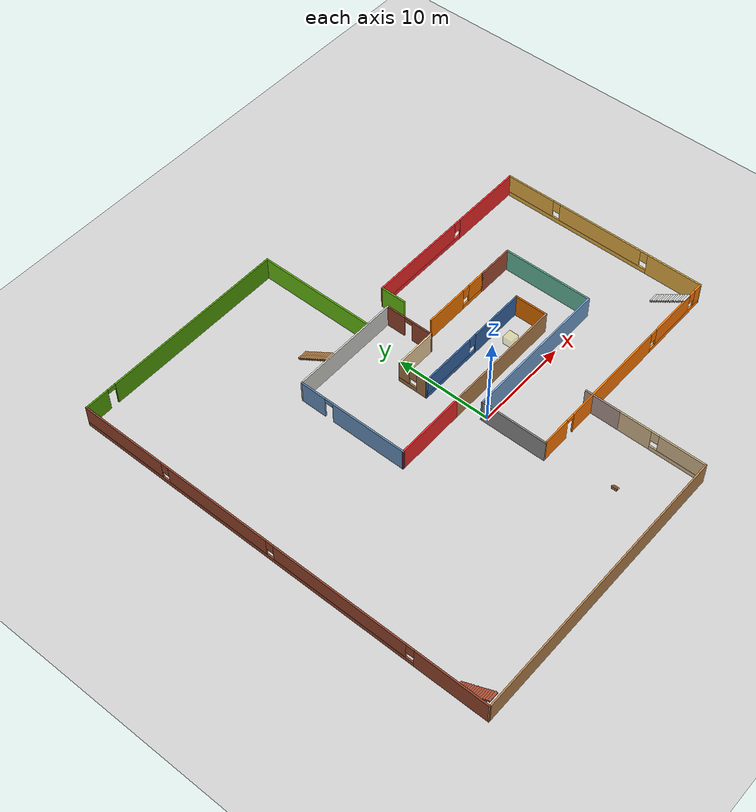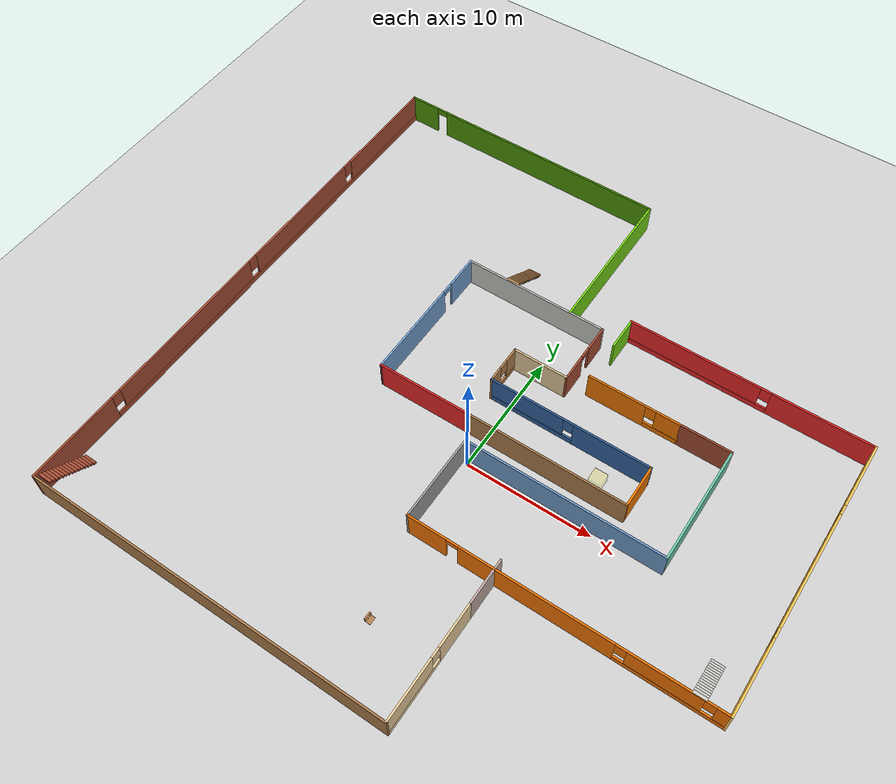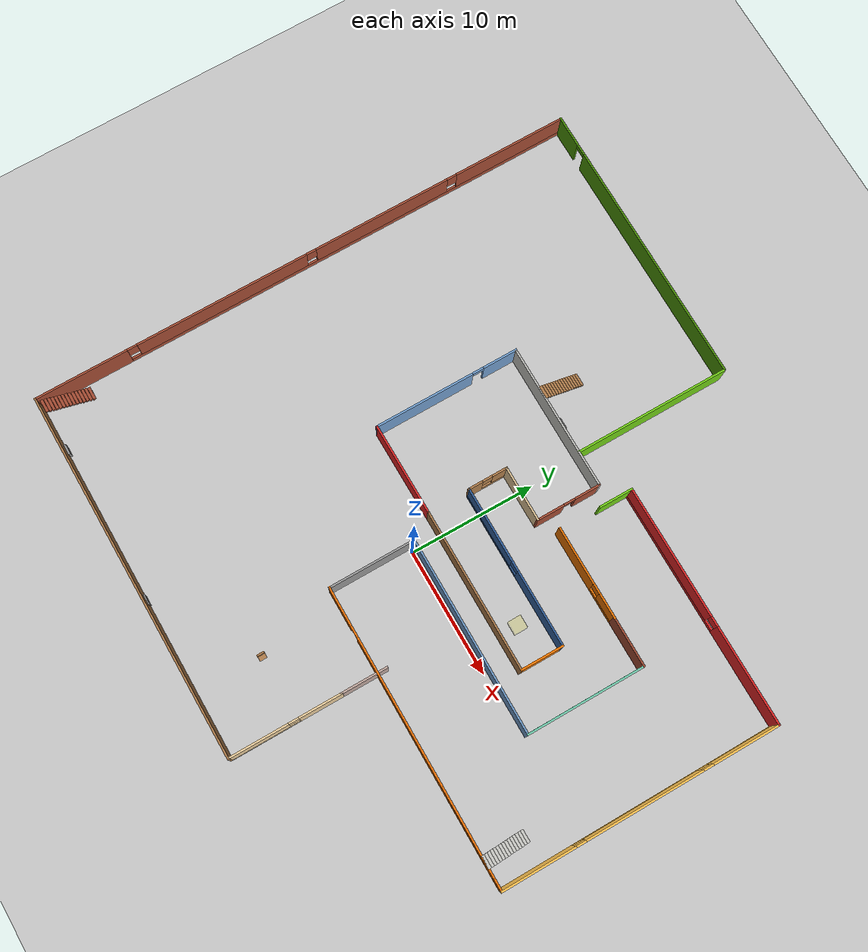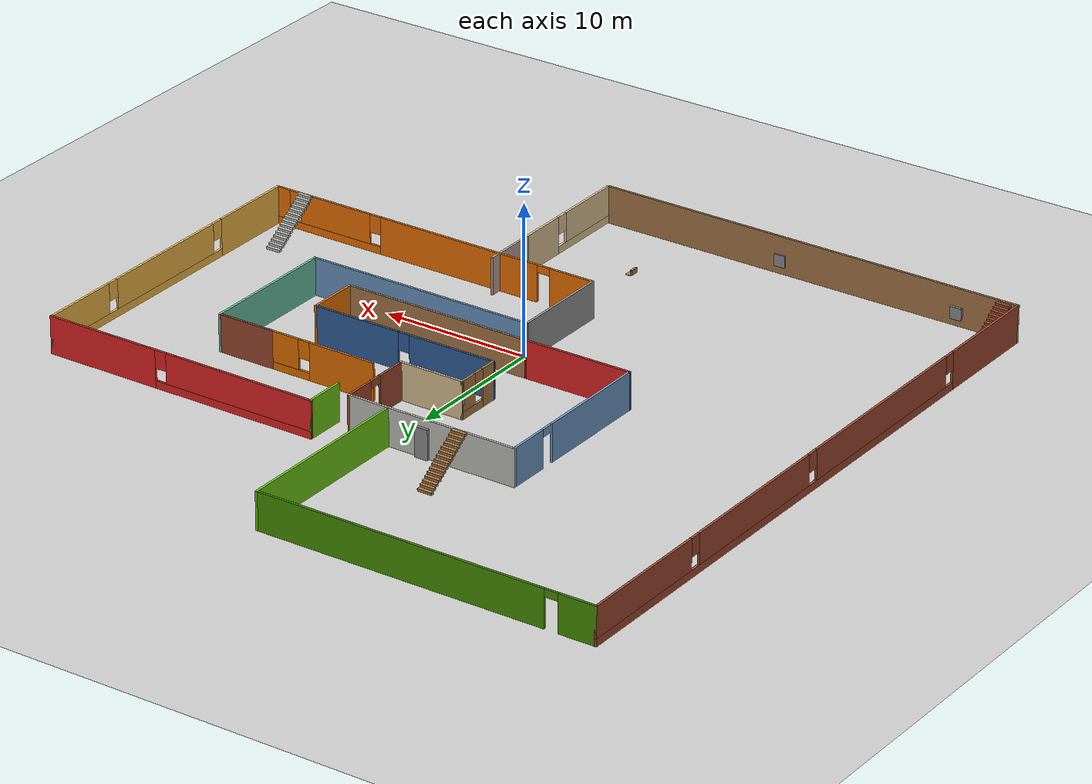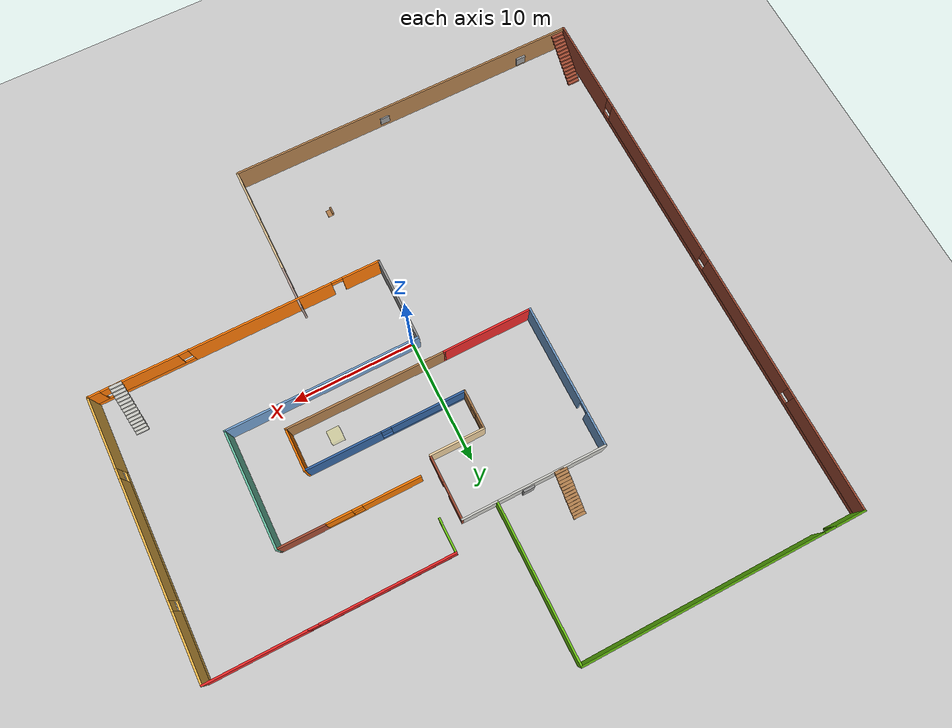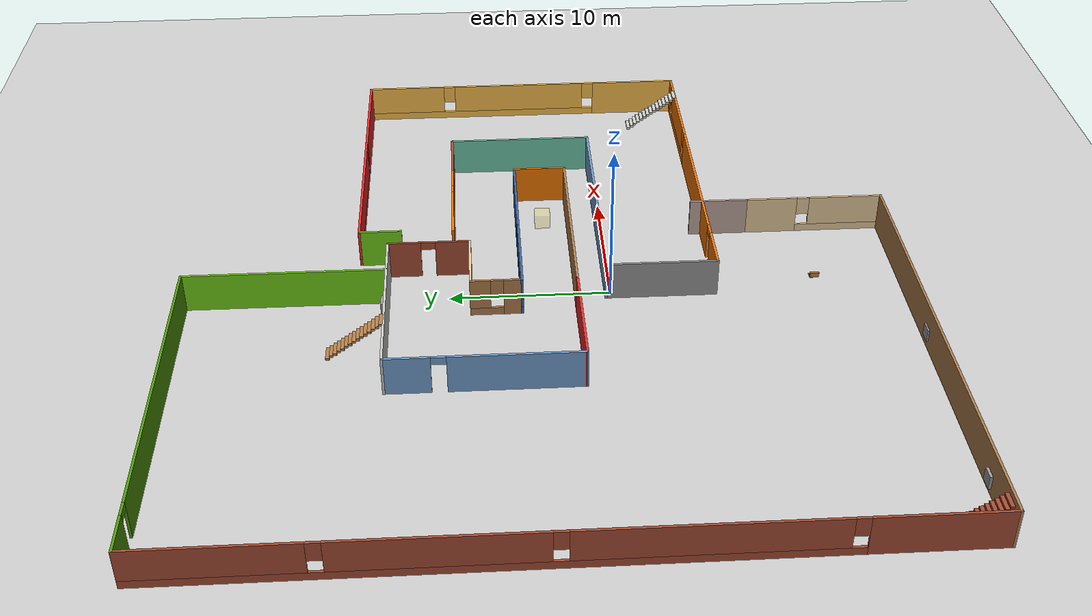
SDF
<sdf version="1.7">
 <world name="default">
  <light name="sun" type="directional">
   <pose>0 0 10 0 -0 0</pose>
   <diffuse>0.8 0.8 0.8 1</diffuse>
   <specular>0.2 0.2 0.2 1</specular>
   <attenuation>
    <range>1000</range>
    <constant>0.9</constant>
    <linear>0.01</linear>
    <quadratic>0.001</quadratic>
   </attenuation>
   <direction>-0.5 0.1 -0.9</direction>
   <spot><inner_angle>0</inner_angle><outer_angle>0</outer_angle><falloff>0</falloff></spot>
  </light>
  <model name="ground_plane">
   <static>1</static>
   <link name="link">
    <collision name="collision">
     <geometry><plane><normal>0 0 1</normal><size>100 100</size></plane></geometry>
     <surface>
      <contact><collide_bitmask>65535</collide_bitmask></contact>
      <friction><ode><mu>100</mu><mu2>50</mu2></ode></friction>
     </surface>
    </collision>
    <visual name="visual">
     <cast_shadows>0</cast_shadows>
     <geometry><plane><normal>0 0 1</normal><size>100 100</size></plane></geometry>
     <material>
      <script><uri>file://media/materials/scripts/gazebo.material</uri><name>Gazebo/Grey</name></script>
     </material>
    </visual>
   </link>
  </model>
  <gravity>0 0 -9.8</gravity>
  <magnetic_field>6e-06 2.3e-05 -4.2e-05</magnetic_field>
  <atmosphere type="adiabatic"/>
  <physics type="ode">
   <max_step_size>0.001</max_step_size>
   <real_time_factor>1</real_time_factor>
   <real_time_update_rate>1000</real_time_update_rate>
  </physics>
  <scene><ambient>0.4 0.4 0.4 1</ambient><background>0.7 0.7 0.7 1</background><shadows>1</shadows></scene>
  <spherical_coordinates>
   <surface_model>EARTH_WGS84</surface_model>
   <latitude_deg>0</latitude_deg>
   <longitude_deg>0</longitude_deg>
   <elevation>0</elevation>
   <heading_deg>0</heading_deg>
  </spherical_coordinates>
  <model name="pavan">
   <pose>0.117796 3.95267 0 0 -0 0</pose>
   <link name="Door_0">
    <collision name="Door_0_Collision">
     <geometry><box><size>0.9 0.17 2</size></box></geometry>
     <pose>0 0 1 0 -0 0</pose>
    </collision>
    <visual name="Door_0_Visual">
     <pose>0 0 1 0 -0 0</pose>
     <geometry><box><size>0.9 0.17 2</size></box></geometry>
     <material>
      <script><uri>file://media/materials/scripts/gazebo.material</uri><name>Gazebo/Grey</name></script>
     </material>
    </visual>
    <pose>-2.70341 9.99929 0 0 -0 0</pose>
   </link>
   <link name="Stairs_1">
    <visual name="Stairs_1_Visual_0">
     <pose>-22.2721 -18.5444 0.083333 0 -0 0</pose>
     <geometry><box><size>1 0.233333 0.166667</size></box></geometry>
     <material>
      <script><uri>file://media/materials/scripts/gazebo.material</uri><name>Gazebo/Bricks</name></script>
      <ambient>1 1 1 1</ambient>
     </material>
     <meta><layer>0</layer></meta>
    </visual>
    <collision name="Stairs_1_Collision_0">
     <geometry><box><size>1 0.233333 0.166667</size></box></geometry>
     <pose>-22.2721 -18.5444 0.083333 0 -0 0</pose>
    </collision>
    <visual name="Stairs_1_Visual_1">
     <pose>-22.2721 -18.7777 0.25 0 -0 0</pose>
     <geometry><box><size>1 0.233333 0.166667</size></box></geometry>
     <material>
      <script><uri>file://media/materials/scripts/gazebo.material</uri><name>Gazebo/Bricks</name></script>
      <ambient>1 1 1 1</ambient>
     </material>
     <meta><layer>0</layer></meta>
    </visual>
    <collision name="Stairs_1_Collision_1">
     <geometry><box><size>1 0.233333 0.166667</size></box></geometry>
     <pose>-22.2721 -18.7777 0.25 0 -0 0</pose>
    </collision>
    <visual name="Stairs_1_Visual_2">
     <pose>-22.2721 -19.0111 0.416667 0 -0 0</pose>
     <geometry><box><size>1 0.233333 0.166667</size></box></geometry>
     <material>
      <script><uri>file://media/materials/scripts/gazebo.material</uri><name>Gazebo/Bricks</name></script>
      <ambient>1 1 1 1</ambient>
     </material>
     <meta><layer>0</layer></meta>
    </visual>
    <collision name="Stairs_1_Collision_2">
     <geometry><box><size>1 0.233333 0.166667</size></box></geometry>
     <pose>-22.2721 -19.0111 0.416667 0 -0 0</pose>
    </collision>
    <visual name="Stairs_1_Visual_3">
     <pose>-22.2721 -19.2444 0.583333 0 -0 0</pose>
     <geometry><box><size>1 0.233333 0.166667</size></box></geometry>
     <material>
      <script><uri>file://media/materials/scripts/gazebo.material</uri><name>Gazebo/Bricks</name></script>
      <ambient>1 1 1 1</ambient>
     </material>
     <meta><layer>0</layer></meta>
    </visual>
    <collision name="Stairs_1_Collision_3">
     <geometry><box><size>1 0.233333 0.166667</size></box></geometry>
     <pose>-22.2721 -19.2444 0.583333 0 -0 0</pose>
    </collision>
    <visual name="Stairs_1_Visual_4">
     <pose>-22.2721 -19.4777 0.75 0 -0 0</pose>
     <geometry><box><size>1 0.233333 0.166667</size></box></geometry>
     <material>
      <script><uri>file://media/materials/scripts/gazebo.material</uri><name>Gazebo/Bricks</name></script>
      <ambient>1 1 1 1</ambient>
     </material>
     <meta><layer>0</layer></meta>
    </visual>
    <collision name="Stairs_1_Collision_4">
     <geometry><box><size>1 0.233333 0.166667</size></box></geometry>
     <pose>-22.2721 -19.4777 0.75 0 -0 0</pose>
    </collision>
    <visual name="Stairs_1_Visual_5">
     <pose>-22.2721 -19.7111 0.916667 0 -0 0</pose>
     <geometry><box><size>1 0.233333 0.166667</size></box></geometry>
     <material>
      <script><uri>file://media/materials/scripts/gazebo.material</uri><name>Gazebo/Bricks</name></script>
      <ambient>1 1 1 1</ambient>
     </material>
     <meta><layer>0</layer></meta>
    </visual>
    <collision name="Stairs_1_Collision_5">
     <geometry><box><size>1 0.233333 0.166667</size></box></geometry>
     <pose>-22.2721 -19.7111 0.916667 0 -0 0</pose>
    </collision>
    <visual name="Stairs_1_Visual_6">
     <pose>-22.2721 -19.9444 1.08333 0 -0 0</pose>
     <geometry><box><size>1 0.233333 0.166667</size></box></geometry>
     <material>
      <script><uri>file://media/materials/scripts/gazebo.material</uri><name>Gazebo/Bricks</name></script>
      <ambient>1 1 1 1</ambient>
     </material>
     <meta><layer>0</layer></meta>
    </visual>
    <collision name="Stairs_1_Collision_6">
     <geometry><box><size>1 0.233333 0.166667</size></box></geometry>
     <pose>-22.2721 -19.9444 1.08333 0 -0 0</pose>
    </collision>
    <visual name="Stairs_1_Visual_7">
     <pose>-22.2721 -20.1777 1.25 0 -0 0</pose>
     <geometry><box><size>1 0.233333 0.166667</size></box></geometry>
     <material>
      <script><uri>file://media/materials/scripts/gazebo.material</uri><name>Gazebo/Bricks</name></script>
      <ambient>1 1 1 1</ambient>
     </material>
     <meta><layer>0</layer></meta>
    </visual>
    <collision name="Stairs_1_Collision_7">
     <geometry><box><size>1 0.233333 0.166667</size></box></geometry>
     <pose>-22.2721 -20.1777 1.25 0 -0 0</pose>
    </collision>
    <visual name="Stairs_1_Visual_8">
     <pose>-22.2721 -20.4111 1.41667 0 -0 0</pose>
     <geometry><box><size>1 0.233333 0.166667</size></box></geometry>
     <material>
      <script><uri>file://media/materials/scripts/gazebo.material</uri><name>Gazebo/Bricks</name></script>
      <ambient>1 1 1 1</ambient>
     </material>
     <meta><layer>0</layer></meta>
    </visual>
    <collision name="Stairs_1_Collision_8">
     <geometry><box><size>1 0.233333 0.166667</size></box></geometry>
     <pose>-22.2721 -20.4111 1.41667 0 -0 0</pose>
    </collision>
    <visual name="Stairs_1_Visual_9">
     <pose>-22.2721 -20.6444 1.58333 0 -0 0</pose>
     <geometry><box><size>1 0.233333 0.166667</size></box></geometry>
     <material>
      <script><uri>file://media/materials/scripts/gazebo.material</uri><name>Gazebo/Bricks</name></script>
      <ambient>1 1 1 1</ambient>
     </material>
     <meta><layer>0</layer></meta>
    </visual>
    <collision name="Stairs_1_Collision_9">
     <geometry><box><size>1 0.233333 0.166667</size></box></geometry>
     <pose>-22.2721 -20.6444 1.58333 0 -0 0</pose>
    </collision>
    <visual name="Stairs_1_Visual_10">
     <pose>-22.2721 -20.8777 1.75 0 -0 0</pose>
     <geometry><box><size>1 0.233333 0.166667</size></box></geometry>
     <material>
      <script><uri>file://media/materials/scripts/gazebo.material</uri><name>Gazebo/Bricks</name></script>
      <ambient>1 1 1 1</ambient>
     </material>
     <meta><layer>0</layer></meta>
    </visual>
    <collision name="Stairs_1_Collision_10">
     <geometry><box><size>1 0.233333 0.166667</size></box></geometry>
     <pose>-22.2721 -20.8777 1.75 0 -0 0</pose>
    </collision>
    <visual name="Stairs_1_Visual_11">
     <pose>-22.2721 -21.1111 1.91667 0 -0 0</pose>
     <geometry><box><size>1 0.233333 0.166667</size></box></geometry>
     <material>
      <script><uri>file://media/materials/scripts/gazebo.material</uri><name>Gazebo/Bricks</name></script>
      <ambient>1 1 1 1</ambient>
     </material>
     <meta><layer>0</layer></meta>
    </visual>
    <collision name="Stairs_1_Collision_11">
     <geometry><box><size>1 0.233333 0.166667</size></box></geometry>
     <pose>-22.2721 -21.1111 1.91667 0 -0 0</pose>
    </collision>
    <visual name="Stairs_1_Visual_12">
     <pose>-22.2721 -21.3444 2.08333 0 -0 0</pose>
     <geometry><box><size>1 0.233333 0.166667</size></box></geometry>
     <material>
      <script><uri>file://media/materials/scripts/gazebo.material</uri><name>Gazebo/Bricks</name></script>
      <ambient>1 1 1 1</ambient>
     </material>
     <meta><layer>0</layer></meta>
    </visual>
    <collision name="Stairs_1_Collision_12">
     <geometry><box><size>1 0.233333 0.166667</size></box></geometry>
     <pose>-22.2721 -21.3444 2.08333 0 -0 0</pose>
    </collision>
    <visual name="Stairs_1_Visual_13">
     <pose>-22.2721 -21.5777 2.25 0 -0 0</pose>
     <geometry><box><size>1 0.233333 0.166667</size></box></geometry>
     <material>
      <script><uri>file://media/materials/scripts/gazebo.material</uri><name>Gazebo/Bricks</name></script>
      <ambient>1 1 1 1</ambient>
     </material>
     <meta><layer>0</layer></meta>
    </visual>
    <collision name="Stairs_1_Collision_13">
     <geometry><box><size>1 0.233333 0.166667</size></box></geometry>
     <pose>-22.2721 -21.5777 2.25 0 -0 0</pose>
    </collision>
    <visual name="Stairs_1_Visual_14">
     <pose>-22.2721 -21.8111 2.41667 0 -0 0</pose>
     <geometry><box><size>1 0.233333 0.166667</size></box></geometry>
     <material>
      <script><uri>file://media/materials/scripts/gazebo.material</uri><name>Gazebo/Bricks</name></script>
      <ambient>1 1 1 1</ambient>
     </material>
     <meta><layer>0</layer></meta>
    </visual>
    <collision name="Stairs_1_Collision_14">
     <geometry><box><size>1 0.233333 0.166667</size></box></geometry>
     <pose>-22.2721 -21.8111 2.41667 0 -0 0</pose>
    </collision>
   </link>
   <link name="Stairs_2">
    <visual name="Stairs_2_Visual_0">
     <pose>-5.2798 13.213 0.083333 0 -0 0</pose>
     <geometry><box><size>1 0.233333 0.166667</size></box></geometry>
     <material>
      <script><uri>file://media/materials/scripts/gazebo.material</uri><name>Gazebo/Wood</name></script>
      <ambient>1 1 1 1</ambient>
     </material>
     <meta><layer>0</layer></meta>
    </visual>
    <collision name="Stairs_2_Collision_0">
     <geometry><box><size>1 0.233333 0.166667</size></box></geometry>
     <pose>-5.2798 13.213 0.083333 0 -0 0</pose>
    </collision>
    <visual name="Stairs_2_Visual_1">
     <pose>-5.2798 12.9797 0.25 0 -0 0</pose>
     <geometry><box><size>1 0.233333 0.166667</size></box></geometry>
     <material>
      <script><uri>file://media/materials/scripts/gazebo.material</uri><name>Gazebo/Wood</name></script>
      <ambient>1 1 1 1</ambient>
     </material>
     <meta><layer>0</layer></meta>
    </visual>
    <collision name="Stairs_2_Collision_1">
     <geometry><box><size>1 0.233333 0.166667</size></box></geometry>
     <pose>-5.2798 12.9797 0.25 0 -0 0</pose>
    </collision>
    <visual name="Stairs_2_Visual_2">
     <pose>-5.2798 12.7463 0.416667 0 -0 0</pose>
     <geometry><box><size>1 0.233333 0.166667</size></box></geometry>
     <material>
      <script><uri>file://media/materials/scripts/gazebo.material</uri><name>Gazebo/Wood</name></script>
      <ambient>1 1 1 1</ambient>
     </material>
     <meta><layer>0</layer></meta>
    </visual>
    <collision name="Stairs_2_Collision_2">
     <geometry><box><size>1 0.233333 0.166667</size></box></geometry>
     <pose>-5.2798 12.7463 0.416667 0 -0 0</pose>
    </collision>
    <visual name="Stairs_2_Visual_3">
     <pose>-5.2798 12.513 0.583333 0 -0 0</pose>
     <geometry><box><size>1 0.233333 0.166667</size></box></geometry>
     <material>
      <script><uri>file://media/materials/scripts/gazebo.material</uri><name>Gazebo/Wood</name></script>
      <ambient>1 1 1 1</ambient>
     </material>
     <meta><layer>0</layer></meta>
    </visual>
    <collision name="Stairs_2_Collision_3">
     <geometry><box><size>1 0.233333 0.166667</size></box></geometry>
     <pose>-5.2798 12.513 0.583333 0 -0 0</pose>
    </collision>
    <visual name="Stairs_2_Visual_4">
     <pose>-5.2798 12.2797 0.75 0 -0 0</pose>
     <geometry><box><size>1 0.233333 0.166667</size></box></geometry>
     <material>
      <script><uri>file://media/materials/scripts/gazebo.material</uri><name>Gazebo/Wood</name></script>
      <ambient>1 1 1 1</ambient>
     </material>
     <meta><layer>0</layer></meta>
    </visual>
    <collision name="Stairs_2_Collision_4">
     <geometry><box><size>1 0.233333 0.166667</size></box></geometry>
     <pose>-5.2798 12.2797 0.75 0 -0 0</pose>
    </collision>
    <visual name="Stairs_2_Visual_5">
     <pose>-5.2798 12.0463 0.916667 0 -0 0</pose>
     <geometry><box><size>1 0.233333 0.166667</size></box></geometry>
     <material>
      <script><uri>file://media/materials/scripts/gazebo.material</uri><name>Gazebo/Wood</name></script>
      <ambient>1 1 1 1</ambient>
     </material>
     <meta><layer>0</layer></meta>
    </visual>
    <collision name="Stairs_2_Collision_5">
     <geometry><box><size>1 0.233333 0.166667</size></box></geometry>
     <pose>-5.2798 12.0463 0.916667 0 -0 0</pose>
    </collision>
    <visual name="Stairs_2_Visual_6">
     <pose>-5.2798 11.813 1.08333 0 -0 0</pose>
     <geometry><box><size>1 0.233333 0.166667</size></box></geometry>
     <material>
      <script><uri>file://media/materials/scripts/gazebo.material</uri><name>Gazebo/Wood</name></script>
      <ambient>1 1 1 1</ambient>
     </material>
     <meta><layer>0</layer></meta>
    </visual>
    <collision name="Stairs_2_Collision_6">
     <geometry><box><size>1 0.233333 0.166667</size></box></geometry>
     <pose>-5.2798 11.813 1.08333 0 -0 0</pose>
    </collision>
    <visual name="Stairs_2_Visual_7">
     <pose>-5.2798 11.5797 1.25 0 -0 0</pose>
     <geometry><box><size>1 0.233333 0.166667</size></box></geometry>
     <material>
      <script><uri>file://media/materials/scripts/gazebo.material</uri><name>Gazebo/Wood</name></script>
      <ambient>1 1 1 1</ambient>
     </material>
     <meta><layer>0</layer></meta>
    </visual>
    <collision name="Stairs_2_Collision_7">
     <geometry><box><size>1 0.233333 0.166667</size></box></geometry>
     <pose>-5.2798 11.5797 1.25 0 -0 0</pose>
    </collision>
    <visual name="Stairs_2_Visual_8">
     <pose>-5.2798 11.3463 1.41667 0 -0 0</pose>
     <geometry><box><size>1 0.233333 0.166667</size></box></geometry>
     <material>
      <script><uri>file://media/materials/scripts/gazebo.material</uri><name>Gazebo/Wood</name></script>
      <ambient>1 1 1 1</ambient>
     </material>
     <meta><layer>0</layer></meta>
    </visual>
    <collision name="Stairs_2_Collision_8">
     <geometry><box><size>1 0.233333 0.166667</size></box></geometry>
     <pose>-5.2798 11.3463 1.41667 0 -0 0</pose>
    </collision>
    <visual name="Stairs_2_Visual_9">
     <pose>-5.2798 11.113 1.58333 0 -0 0</pose>
     <geometry><box><size>1 0.233333 0.166667</size></box></geometry>
     <material>
      <script><uri>file://media/materials/scripts/gazebo.material</uri><name>Gazebo/Wood</name></script>
      <ambient>1 1 1 1</ambient>
     </material>
     <meta><layer>0</layer></meta>
    </visual>
    <collision name="Stairs_2_Collision_9">
     <geometry><box><size>1 0.233333 0.166667</size></box></geometry>
     <pose>-5.2798 11.113 1.58333 0 -0 0</pose>
    </collision>
    <visual name="Stairs_2_Visual_10">
     <pose>-5.2798 10.8797 1.75 0 -0 0</pose>
     <geometry><box><size>1 0.233333 0.166667</size></box></geometry>
     <material>
      <script><uri>file://media/materials/scripts/gazebo.material</uri><name>Gazebo/Wood</name></script>
      <ambient>1 1 1 1</ambient>
     </material>
     <meta><layer>0</layer></meta>
    </visual>
    <collision name="Stairs_2_Collision_10">
     <geometry><box><size>1 0.233333 0.166667</size></box></geometry>
     <pose>-5.2798 10.8797 1.75 0 -0 0</pose>
    </collision>
    <visual name="Stairs_2_Visual_11">
     <pose>-5.2798 10.6463 1.91667 0 -0 0</pose>
     <geometry><box><size>1 0.233333 0.166667</size></box></geometry>
     <material>
      <script><uri>file://media/materials/scripts/gazebo.material</uri><name>Gazebo/Wood</name></script>
      <ambient>1 1 1 1</ambient>
     </material>
     <meta><layer>0</layer></meta>
    </visual>
    <collision name="Stairs_2_Collision_11">
     <geometry><box><size>1 0.233333 0.166667</size></box></geometry>
     <pose>-5.2798 10.6463 1.91667 0 -0 0</pose>
    </collision>
    <visual name="Stairs_2_Visual_12">
     <pose>-5.2798 10.413 2.08333 0 -0 0</pose>
     <geometry><box><size>1 0.233333 0.166667</size></box></geometry>
     <material>
      <script><uri>file://media/materials/scripts/gazebo.material</uri><name>Gazebo/Wood</name></script>
      <ambient>1 1 1 1</ambient>
     </material>
     <meta><layer>0</layer></meta>
    </visual>
    <collision name="Stairs_2_Collision_12">
     <geometry><box><size>1 0.233333 0.166667</size></box></geometry>
     <pose>-5.2798 10.413 2.08333 0 -0 0</pose>
    </collision>
    <visual name="Stairs_2_Visual_13">
     <pose>-5.2798 10.1797 2.25 0 -0 0</pose>
     <geometry><box><size>1 0.233333 0.166667</size></box></geometry>
     <material>
      <script><uri>file://media/materials/scripts/gazebo.material</uri><name>Gazebo/Wood</name></script>
      <ambient>1 1 1 1</ambient>
     </material>
     <meta><layer>0</layer></meta>
    </visual>
    <collision name="Stairs_2_Collision_13">
     <geometry><box><size>1 0.233333 0.166667</size></box></geometry>
     <pose>-5.2798 10.1797 2.25 0 -0 0</pose>
    </collision>
    <visual name="Stairs_2_Visual_14">
     <pose>-5.2798 9.94634 2.41667 0 -0 0</pose>
     <geometry><box><size>1 0.233333 0.166667</size></box></geometry>
     <material>
      <script><uri>file://media/materials/scripts/gazebo.material</uri><name>Gazebo/Wood</name></script>
      <ambient>1 1 1 1</ambient>
     </material>
     <meta><layer>0</layer></meta>
    </visual>
    <collision name="Stairs_2_Collision_14">
     <geometry><box><size>1 0.233333 0.166667</size></box></geometry>
     <pose>-5.2798 9.94634 2.41667 0 -0 0</pose>
    </collision>
   </link>
   <link name="Stairs_3">
    <visual name="Stairs_3_Visual_0">
     <pose>20.8948 -7.10954 0.083333 0 -0 0</pose>
     <geometry><box><size>1 0.233333 0.166667</size></box></geometry>
     <material>
      <script><uri>file://media/materials/scripts/gazebo.material</uri><name>Gazebo/CeilingTiled</name></script>
      <ambient>1 1 1 1</ambient>
     </material>
     <meta><layer>0</layer></meta>
    </visual>
    <collision name="Stairs_3_Collision_0">
     <geometry><box><size>1 0.233333 0.166667</size></box></geometry>
     <pose>20.8948 -7.10954 0.083333 0 -0 0</pose>
    </collision>
    <visual name="Stairs_3_Visual_1">
     <pose>20.8948 -7.34288 0.25 0 -0 0</pose>
     <geometry><box><size>1 0.233333 0.166667</size></box></geometry>
     <material>
      <script><uri>file://media/materials/scripts/gazebo.material</uri><name>Gazebo/CeilingTiled</name></script>
      <ambient>1 1 1 1</ambient>
     </material>
     <meta><layer>0</layer></meta>
    </visual>
    <collision name="Stairs_3_Collision_1">
     <geometry><box><size>1 0.233333 0.166667</size></box></geometry>
     <pose>20.8948 -7.34288 0.25 0 -0 0</pose>
    </collision>
    <visual name="Stairs_3_Visual_2">
     <pose>20.8948 -7.57621 0.416667 0 -0 0</pose>
     <geometry><box><size>1 0.233333 0.166667</size></box></geometry>
     <material>
      <script><uri>file://media/materials/scripts/gazebo.material</uri><name>Gazebo/CeilingTiled</name></script>
      <ambient>1 1 1 1</ambient>
     </material>
     <meta><layer>0</layer></meta>
    </visual>
    <collision name="Stairs_3_Collision_2">
     <geometry><box><size>1 0.233333 0.166667</size></box></geometry>
     <pose>20.8948 -7.57621 0.416667 0 -0 0</pose>
    </collision>
    <visual name="Stairs_3_Visual_3">
     <pose>20.8948 -7.80954 0.583333 0 -0 0</pose>
     <geometry><box><size>1 0.233333 0.166667</size></box></geometry>
     <material>
      <script><uri>file://media/materials/scripts/gazebo.material</uri><name>Gazebo/CeilingTiled</name></script>
      <ambient>1 1 1 1</ambient>
     </material>
     <meta><layer>0</layer></meta>
    </visual>
    <collision name="Stairs_3_Collision_3">
     <geometry><box><size>1 0.233333 0.166667</size></box></geometry>
     <pose>20.8948 -7.80954 0.583333 0 -0 0</pose>
    </collision>
    <visual name="Stairs_3_Visual_4">
     <pose>20.8948 -8.04287 0.75 0 -0 0</pose>
     <geometry><box><size>1 0.233333 0.166667</size></box></geometry>
     <material>
      <script><uri>file://media/materials/scripts/gazebo.material</uri><name>Gazebo/CeilingTiled</name></script>
      <ambient>1 1 1 1</ambient>
     </material>
     <meta><layer>0</layer></meta>
    </visual>
    <collision name="Stairs_3_Collision_4">
     <geometry><box><size>1 0.233333 0.166667</size></box></geometry>
     <pose>20.8948 -8.04287 0.75 0 -0 0</pose>
    </collision>
    <visual name="Stairs_3_Visual_5">
     <pose>20.8948 -8.27621 0.916667 0 -0 0</pose>
     <geometry><box><size>1 0.233333 0.166667</size></box></geometry>
     <material>
      <script><uri>file://media/materials/scripts/gazebo.material</uri><name>Gazebo/CeilingTiled</name></script>
      <ambient>1 1 1 1</ambient>
     </material>
     <meta><layer>0</layer></meta>
    </visual>
    <collision name="Stairs_3_Collision_5">
     <geometry><box><size>1 0.233333 0.166667</size></box></geometry>
     <pose>20.8948 -8.27621 0.916667 0 -0 0</pose>
    </collision>
    <visual name="Stairs_3_Visual_6">
     <pose>20.8948 -8.50954 1.08333 0 -0 0</pose>
     <geometry><box><size>1 0.233333 0.166667</size></box></geometry>
     <material>
      <script><uri>file://media/materials/scripts/gazebo.material</uri><name>Gazebo/CeilingTiled</name></script>
      <ambient>1 1 1 1</ambient>
     </material>
     <meta><layer>0</layer></meta>
    </visual>
    <collision name="Stairs_3_Collision_6">
     <geometry><box><size>1 0.233333 0.166667</size></box></geometry>
     <pose>20.8948 -8.50954 1.08333 0 -0 0</pose>
    </collision>
    <visual name="Stairs_3_Visual_7">
     <pose>20.8948 -8.74287 1.25 0 -0 0</pose>
     <geometry><box><size>1 0.233333 0.166667</size></box></geometry>
     <material>
      <script><uri>file://media/materials/scripts/gazebo.material</uri><name>Gazebo/CeilingTiled</name></script>
      <ambient>1 1 1 1</ambient>
     </material>
     <meta><layer>0</layer></meta>
    </visual>
    <collision name="Stairs_3_Collision_7">
     <geometry><box><size>1 0.233333 0.166667</size></box></geometry>
     <pose>20.8948 -8.74287 1.25 0 -0 0</pose>
    </collision>
    <visual name="Stairs_3_Visual_8">
     <pose>20.8948 -8.97621 1.41667 0 -0 0</pose>
     <geometry><box><size>1 0.233333 0.166667</size></box></geometry>
     <material>
      <script><uri>file://media/materials/scripts/gazebo.material</uri><name>Gazebo/CeilingTiled</name></script>
      <ambient>1 1 1 1</ambient>
     </material>
     <meta><layer>0</layer></meta>
    </visual>
    <collision name="Stairs_3_Collision_8">
     <geometry><box><size>1 0.233333 0.166667</size></box></geometry>
     <pose>20.8948 -8.97621 1.41667 0 -0 0</pose>
    </collision>
    <visual name="Stairs_3_Visual_9">
     <pose>20.8948 -9.20954 1.58333 0 -0 0</pose>
     <geometry><box><size>1 0.233333 0.166667</size></box></geometry>
     <material>
      <script><uri>file://media/materials/scripts/gazebo.material</uri><name>Gazebo/CeilingTiled</name></script>
      <ambient>1 1 1 1</ambient>
     </material>
     <meta><layer>0</layer></meta>
    </visual>
    <collision name="Stairs_3_Collision_9">
     <geometry><box><size>1 0.233333 0.166667</size></box></geometry>
     <pose>20.8948 -9.20954 1.58333 0 -0 0</pose>
    </collision>
    <visual name="Stairs_3_Visual_10">
     <pose>20.8948 -9.44287 1.75 0 -0 0</pose>
     <geometry><box><size>1 0.233333 0.166667</size></box></geometry>
     <material>
      <script><uri>file://media/materials/scripts/gazebo.material</uri><name>Gazebo/CeilingTiled</name></script>
      <ambient>1 1 1 1</ambient>
     </material>
     <meta><layer>0</layer></meta>
    </visual>
    <collision name="Stairs_3_Collision_10">
     <geometry><box><size>1 0.233333 0.166667</size></box></geometry>
     <pose>20.8948 -9.44287 1.75 0 -0 0</pose>
    </collision>
    <visual name="Stairs_3_Visual_11">
     <pose>20.8948 -9.67621 1.91667 0 -0 0</pose>
     <geometry><box><size>1 0.233333 0.166667</size></box></geometry>
     <material>
      <script><uri>file://media/materials/scripts/gazebo.material</uri><name>Gazebo/CeilingTiled</name></script>
      <ambient>1 1 1 1</ambient>
     </material>
     <meta><layer>0</layer></meta>
    </visual>
    <collision name="Stairs_3_Collision_11">
     <geometry><box><size>1 0.233333 0.166667</size></box></geometry>
     <pose>20.8948 -9.67621 1.91667 0 -0 0</pose>
    </collision>
    <visual name="Stairs_3_Visual_12">
     <pose>20.8948 -9.90954 2.08333 0 -0 0</pose>
     <geometry><box><size>1 0.233333 0.166667</size></box></geometry>
     <material>
      <script><uri>file://media/materials/scripts/gazebo.material</uri><name>Gazebo/CeilingTiled</name></script>
      <ambient>1 1 1 1</ambient>
     </material>
     <meta><layer>0</layer></meta>
    </visual>
    <collision name="Stairs_3_Collision_12">
     <geometry><box><size>1 0.233333 0.166667</size></box></geometry>
     <pose>20.8948 -9.90954 2.08333 0 -0 0</pose>
    </collision>
    <visual name="Stairs_3_Visual_13">
     <pose>20.8948 -10.1429 2.25 0 -0 0</pose>
     <geometry><box><size>1 0.233333 0.166667</size></box></geometry>
     <material>
      <script><uri>file://media/materials/scripts/gazebo.material</uri><name>Gazebo/CeilingTiled</name></script>
      <ambient>1 1 1 1</ambient>
     </material>
     <meta><layer>0</layer></meta>
    </visual>
    <collision name="Stairs_3_Collision_13">
     <geometry><box><size>1 0.233333 0.166667</size></box></geometry>
     <pose>20.8948 -10.1429 2.25 0 -0 0</pose>
    </collision>
    <visual name="Stairs_3_Visual_14">
     <pose>20.8948 -10.3762 2.41667 0 -0 0</pose>
     <geometry><box><size>1 0.233333 0.166667</size></box></geometry>
     <material>
      <script><uri>file://media/materials/scripts/gazebo.material</uri><name>Gazebo/CeilingTiled</name></script>
      <ambient>1 1 1 1</ambient>
     </material>
     <meta><layer>0</layer></meta>
    </visual>
    <collision name="Stairs_3_Collision_14">
     <geometry><box><size>1 0.233333 0.166667</size></box></geometry>
     <pose>20.8948 -10.3762 2.41667 0 -0 0</pose>
    </collision>
   </link>
   <link name="Wall_0">
    <collision name="Wall_0_Collision">
     <geometry><box><size>13 0.15 2.5</size></box></geometry>
     <pose>0 0 1.25 0 -0 0</pose>
    </collision>
    <visual name="Wall_0_Visual">
     <pose>0 0 1.25 0 -0 0</pose>
     <geometry><box><size>13 0.15 2.5</size></box></geometry>
     <material>
      <script><uri>file://media/materials/scripts/gazebo.material</uri><name>Gazebo/Wood</name></script>
      <ambient>0.937255 0.160784 0.160784 1</ambient>
     </material>
     <meta><layer>0</layer></meta>
    </visual>
    <pose>4.64523 -1.73876 0 0 -0 0</pose>
   </link>
   <link name="Wall_1">
    <collision name="Wall_1_Collision">
     <geometry><box><size>3.5 0.15 2.5</size></box></geometry>
     <pose>0 0 1.25 0 -0 0</pose>
    </collision>
    <visual name="Wall_1_Visual">
     <pose>0 0 1.25 0 -0 0</pose>
     <geometry><box><size>3.5 0.15 2.5</size></box></geometry>
     <material>
      <script><uri>file://media/materials/scripts/gazebo.material</uri><name>Gazebo/Grey</name></script>
      <ambient>0.960784 0.47451 0 1</ambient>
     </material>
     <meta><layer>0</layer></meta>
    </visual>
    <pose>11.0702 -0.063756 0 0 -0 1.5708</pose>
   </link>
   <link name="Wall_10">
    <pose>7.5403 5.74557 0 0 -0 0</pose>
    <visual name="Wall_10_Visual_0">
     <pose>-1.42681 0 1.25 0 -0 0</pose>
     <geometry><box><size>4.64637 0.15 2.5</size></box></geometry>
     <material>
      <script><uri>file://media/materials/scripts/gazebo.material</uri><name>Gazebo/Grey</name></script>
      <ambient>0.960784 0.47451 0 1</ambient>
     </material>
     <meta><layer>0</layer></meta>
    </visual>
    <collision name="Wall_10_Collision_0">
     <geometry><box><size>4.64637 0.15 2.5</size></box></geometry>
     <pose>-1.42681 0 1.25 0 -0 0</pose>
    </collision>
    <visual name="Wall_10_Visual_1">
     <pose>2.32319 0 0.25 0 -0 0</pose>
     <geometry><box><size>2.85363 0.15 0.5</size></box></geometry>
     <material>
      <script><uri>file://media/materials/scripts/gazebo.material</uri><name>Gazebo/Grey</name></script>
      <ambient>0.960784 0.47451 0 1</ambient>
     </material>
     <meta><layer>0</layer></meta>
    </visual>
    <collision name="Wall_10_Collision_1">
     <geometry><box><size>2.85363 0.15 0.5</size></box></geometry>
     <pose>2.32319 0 0.25 0 -0 0</pose>
    </collision>
    <visual name="Wall_10_Visual_2">
     <pose>2.72319 0 1.5 0 -0 0</pose>
     <geometry><box><size>2.05362 0.15 2</size></box></geometry>
     <material>
      <script><uri>file://media/materials/scripts/gazebo.material</uri><name>Gazebo/Grey</name></script>
      <ambient>0.960784 0.47451 0 1</ambient>
     </material>
     <meta><layer>0</layer></meta>
    </visual>
    <collision name="Wall_10_Collision_2">
     <geometry><box><size>2.05362 0.15 2</size></box></geometry>
     <pose>2.72319 0 1.5 0 -0 0</pose>
    </collision>
    <visual name="Wall_10_Visual_3">
     <pose>1.29638 0 1.9 0 -0 0</pose>
     <geometry><box><size>0.8 0.15 1.2</size></box></geometry>
     <material>
      <script><uri>file://media/materials/scripts/gazebo.material</uri><name>Gazebo/Grey</name></script>
      <ambient>0.960784 0.47451 0 1</ambient>
     </material>
     <meta><layer>0</layer></meta>
    </visual>
    <collision name="Wall_10_Collision_3">
     <geometry><box><size>0.8 0.15 1.2</size></box></geometry>
     <pose>1.29638 0 1.9 0 -0 0</pose>
    </collision>
   </link>
   <link name="Wall_11">
    <collision name="Wall_11_Collision">
     <geometry><box><size>4 0.15 2.5</size></box></geometry>
     <pose>0 0 1.25 0 -0 0</pose>
    </collision>
    <visual name="Wall_11_Visual">
     <pose>0 0 1.25 0 -0 0</pose>
     <geometry><box><size>4 0.15 2.5</size></box></geometry>
     <material>
      <script><uri>file://media/materials/scripts/gazebo.material</uri><name>Gazebo/Bricks</name></script>
      <ambient>1 1 1 1</ambient>
     </material>
     <meta><layer>0</layer></meta>
    </visual>
    <pose>13.1403 5.74557 0 0 -0 0</pose>
   </link>
   <link name="Wall_12">
    <collision name="Wall_12_Collision">
     <geometry><box><size>9.5 0.15 2.5</size></box></geometry>
     <pose>0 0 1.25 0 -0 0</pose>
    </collision>
    <visual name="Wall_12_Visual">
     <pose>0 0 1.25 0 -0 0</pose>
     <geometry><box><size>9.5 0.15 2.5</size></box></geometry>
     <material>
      <script><uri>file://media/materials/scripts/gazebo.material</uri><name>Gazebo/Grey</name></script>
      <ambient>0.435294 0.796078 0.67451 1</ambient>
     </material>
     <meta><layer>0</layer></meta>
    </visual>
    <pose>15.0653 1.07057 0 0 -0 -1.5708</pose>
   </link>
   <link name="Wall_13">
    <collision name="Wall_13_Collision">
     <geometry><box><size>15.75 0.15 2.5</size></box></geometry>
     <pose>0 0 1.25 0 -0 0</pose>
    </collision>
    <visual name="Wall_13_Visual">
     <pose>0 0 1.25 0 -0 0</pose>
     <geometry><box><size>15.75 0.15 2.5</size></box></geometry>
     <material>
      <script><uri>file://media/materials/scripts/gazebo.material</uri><name>Gazebo/Grey</name></script>
      <ambient>0.447059 0.623529 0.811765 1</ambient>
     </material>
     <meta><layer>0</layer></meta>
    </visual>
    <pose>7.2653 -3.60443 0 0 -0 3.14159</pose>
   </link>
   <link name="Wall_14">
    <collision name="Wall_14_Collision">
     <geometry><box><size>7 0.15 2.5</size></box></geometry>
     <pose>0 0 1.25 0 -0 0</pose>
    </collision>
    <visual name="Wall_14_Visual">
     <pose>0 0 1.25 0 -0 0</pose>
     <geometry><box><size>7 0.15 2.5</size></box></geometry>
     <material>
      <script><uri>file://media/materials/scripts/gazebo.material</uri><name>Gazebo/Grey</name></script>
      <ambient>0.333333 0.341176 0.32549 1</ambient>
     </material>
     <meta><layer>0</layer></meta>
    </visual>
    <pose>-0.534699 -7.02943 0 0 -0 -1.5708</pose>
   </link>
   <link name="Wall_15">
    <pose>11.2653 -10.4544 0 0 -0 0</pose>
    <visual name="Wall_15_Visual_0">
     <pose>-10.2863 0 1.25 0 -0 0</pose>
     <geometry><box><size>3.17738 0.15 2.5</size></box></geometry>
     <material>
      <script><uri>file://media/materials/scripts/gazebo.material</uri><name>Gazebo/Grey</name></script>
      <ambient>0.996078 0.47451 0.0196078 1</ambient>
     </material>
     <meta><layer>0</layer></meta>
    </visual>
    <collision name="Wall_15_Collision_0">
     <geometry><box><size>3.17738 0.15 2.5</size></box></geometry>
     <pose>-10.2863 0 1.25 0 -0 0</pose>
    </collision>
    <visual name="Wall_15_Visual_1">
     <pose>-1.95398 0 1.25 0 -0 0</pose>
     <geometry><box><size>11.6873 0.15 2.5</size></box></geometry>
     <material>
      <script><uri>file://media/materials/scripts/gazebo.material</uri><name>Gazebo/Grey</name></script>
      <ambient>0.996078 0.47451 0.0196078 1</ambient>
     </material>
     <meta><layer>0</layer></meta>
    </visual>
    <collision name="Wall_15_Collision_1">
     <geometry><box><size>11.6873 0.15 2.5</size></box></geometry>
     <pose>-1.95398 0 1.25 0 -0 0</pose>
    </collision>
    <visual name="Wall_15_Visual_2">
     <pose>3.88967 0 1.25 0 -0 0</pose>
     <geometry><box><size>0 0.15 2.5</size></box></geometry>
     <material>
      <script><uri>file://media/materials/scripts/gazebo.material</uri><name>Gazebo/Grey</name></script>
      <ambient>0.996078 0.47451 0.0196078 1</ambient>
     </material>
     <meta><layer>0</layer></meta>
    </visual>
    <collision name="Wall_15_Collision_2">
     <geometry><box><size>0 0.15 2.5</size></box></geometry>
     <pose>3.88967 0 1.25 0 -0 0</pose>
    </collision>
    <visual name="Wall_15_Visual_3">
     <pose>7.88234 0 0.25 0 -0 0</pose>
     <geometry><box><size>7.98532 0.15 0.5</size></box></geometry>
     <material>
      <script><uri>file://media/materials/scripts/gazebo.material</uri><name>Gazebo/Grey</name></script>
      <ambient>0.996078 0.47451 0.0196078 1</ambient>
     </material>
     <meta><layer>0</layer></meta>
    </visual>
    <collision name="Wall_15_Collision_3">
     <geometry><box><size>7.98532 0.15 0.5</size></box></geometry>
     <pose>7.88234 0 0.25 0 -0 0</pose>
    </collision>
    <visual name="Wall_15_Visual_4">
     <pose>7.35787 0 1.5 0 -0 0</pose>
     <geometry><box><size>5.3364 0.15 2</size></box></geometry>
     <material>
      <script><uri>file://media/materials/scripts/gazebo.material</uri><name>Gazebo/Grey</name></script>
      <ambient>0.996078 0.47451 0.0196078 1</ambient>
     </material>
     <meta><layer>0</layer></meta>
    </visual>
    <collision name="Wall_15_Collision_4">
     <geometry><box><size>5.3364 0.15 2</size></box></geometry>
     <pose>7.35787 0 1.5 0 -0 0</pose>
    </collision>
    <visual name="Wall_15_Visual_5">
     <pose>11.3505 0 1.5 0 -0 0</pose>
     <geometry><box><size>1.04893 0.15 2</size></box></geometry>
     <material>
      <script><uri>file://media/materials/scripts/gazebo.material</uri><name>Gazebo/Grey</name></script>
      <ambient>0.996078 0.47451 0.0196078 1</ambient>
     </material>
     <meta><layer>0</layer></meta>
    </visual>
    <collision name="Wall_15_Collision_5">
     <geometry><box><size>1.04893 0.15 2</size></box></geometry>
     <pose>11.3505 0 1.5 0 -0 0</pose>
    </collision>
    <visual name="Wall_15_Visual_6">
     <pose>3.88967 0 1.9 0 -0 0</pose>
     <geometry><box><size>0 0.15 1.2</size></box></geometry>
     <material>
      <script><uri>file://media/materials/scripts/gazebo.material</uri><name>Gazebo/Grey</name></script>
      <ambient>0.996078 0.47451 0.0196078 1</ambient>
     </material>
     <meta><layer>0</layer></meta>
    </visual>
    <collision name="Wall_15_Collision_6">
     <geometry><box><size>0 0.15 1.2</size></box></geometry>
     <pose>3.88967 0 1.9 0 -0 0</pose>
    </collision>
    <visual name="Wall_15_Visual_7">
     <pose>4.28967 0 1.9 0 -0 0</pose>
     <geometry><box><size>0.8 0.15 1.2</size></box></geometry>
     <material>
      <script><uri>file://media/materials/scripts/gazebo.material</uri><name>Gazebo/Grey</name></script>
      <ambient>0.996078 0.47451 0.0196078 1</ambient>
     </material>
     <meta><layer>0</layer></meta>
    </visual>
    <collision name="Wall_15_Collision_7">
     <geometry><box><size>0.8 0.15 1.2</size></box></geometry>
     <pose>4.28967 0 1.9 0 -0 0</pose>
    </collision>
    <visual name="Wall_15_Visual_8">
     <pose>10.4261 0 1.9 0 -0 0</pose>
     <geometry><box><size>0.8 0.15 1.2</size></box></geometry>
     <material>
      <script><uri>file://media/materials/scripts/gazebo.material</uri><name>Gazebo/Grey</name></script>
      <ambient>0.996078 0.47451 0.0196078 1</ambient>
     </material>
     <meta><layer>0</layer></meta>
    </visual>
    <collision name="Wall_15_Collision_8">
     <geometry><box><size>0.8 0.15 1.2</size></box></geometry>
     <pose>10.4261 0 1.9 0 -0 0</pose>
    </collision>
    <visual name="Wall_15_Visual_9">
     <pose>-8.24762 0 2.25 0 -0 0</pose>
     <geometry><box><size>0.9 0.15 0.5</size></box></geometry>
     <material>
      <script><uri>file://media/materials/scripts/gazebo.material</uri><name>Gazebo/Grey</name></script>
      <ambient>0.996078 0.47451 0.0196078 1</ambient>
     </material>
     <meta><layer>0</layer></meta>
    </visual>
    <collision name="Wall_15_Collision_9">
     <geometry><box><size>0.9 0.15 0.5</size></box></geometry>
     <pose>-8.24762 0 2.25 0 -0 0</pose>
    </collision>
   </link>
   <link name="Wall_16">
    <pose>23.0653 0.595573 0 0 -0 1.5708</pose>
    <visual name="Wall_16_Visual_0">
     <pose>-8.17212 0 1.25 0 -0 0</pose>
     <geometry><box><size>5.90576 0.15 2.5</size></box></geometry>
     <material>
      <script><uri>file://media/materials/scripts/gazebo.material</uri><name>Gazebo/Grey</name></script>
      <ambient>1 0.764706 0.305882 1</ambient>
     </material>
     <meta><layer>0</layer></meta>
    </visual>
    <collision name="Wall_16_Collision_0">
     <geometry><box><size>5.90576 0.15 2.5</size></box></geometry>
     <pose>-8.17212 0 1.25 0 -0 0</pose>
    </collision>
    <visual name="Wall_16_Visual_1">
     <pose>2.95288 0 0.25 0 -0 0</pose>
     <geometry><box><size>16.3442 0.15 0.5</size></box></geometry>
     <material>
      <script><uri>file://media/materials/scripts/gazebo.material</uri><name>Gazebo/Grey</name></script>
      <ambient>1 0.764706 0.305882 1</ambient>
     </material>
     <meta><layer>0</layer></meta>
    </visual>
    <collision name="Wall_16_Collision_1">
     <geometry><box><size>16.3442 0.15 0.5</size></box></geometry>
     <pose>2.95288 0 0.25 0 -0 0</pose>
    </collision>
    <visual name="Wall_16_Visual_2">
     <pose>0.259157 0 1.5 0 -0 0</pose>
     <geometry><box><size>9.3568 0.15 2</size></box></geometry>
     <material>
      <script><uri>file://media/materials/scripts/gazebo.material</uri><name>Gazebo/Grey</name></script>
      <ambient>1 0.764706 0.305882 1</ambient>
     </material>
     <meta><layer>0</layer></meta>
    </visual>
    <collision name="Wall_16_Collision_2">
     <geometry><box><size>9.3568 0.15 2</size></box></geometry>
     <pose>0.259157 0 1.5 0 -0 0</pose>
    </collision>
    <visual name="Wall_16_Visual_3">
     <pose>8.43128 0 1.5 0 -0 0</pose>
     <geometry><box><size>5.38744 0.15 2</size></box></geometry>
     <material>
      <script><uri>file://media/materials/scripts/gazebo.material</uri><name>Gazebo/Grey</name></script>
      <ambient>1 0.764706 0.305882 1</ambient>
     </material>
     <meta><layer>0</layer></meta>
    </visual>
    <collision name="Wall_16_Collision_3">
     <geometry><box><size>5.38744 0.15 2</size></box></geometry>
     <pose>8.43128 0 1.5 0 -0 0</pose>
    </collision>
    <visual name="Wall_16_Visual_4">
     <pose>-4.81924 0 1.9 0 -0 0</pose>
     <geometry><box><size>0.8 0.15 1.2</size></box></geometry>
     <material>
      <script><uri>file://media/materials/scripts/gazebo.material</uri><name>Gazebo/Grey</name></script>
      <ambient>1 0.764706 0.305882 1</ambient>
     </material>
     <meta><layer>0</layer></meta>
    </visual>
    <collision name="Wall_16_Collision_4">
     <geometry><box><size>0.8 0.15 1.2</size></box></geometry>
     <pose>-4.81924 0 1.9 0 -0 0</pose>
    </collision>
    <visual name="Wall_16_Visual_5">
     <pose>5.33756 0 1.9 0 -0 0</pose>
     <geometry><box><size>0.8 0.15 1.2</size></box></geometry>
     <material>
      <script><uri>file://media/materials/scripts/gazebo.material</uri><name>Gazebo/Grey</name></script>
      <ambient>1 0.764706 0.305882 1</ambient>
     </material>
     <meta><layer>0</layer></meta>
    </visual>
    <collision name="Wall_16_Collision_5">
     <geometry><box><size>0.8 0.15 1.2</size></box></geometry>
     <pose>5.33756 0 1.9 0 -0 0</pose>
    </collision>
   </link>
   <link name="Wall_17">
    <pose>13.5153 11.6456 0 0 -0 3.14159</pose>
    <visual name="Wall_17_Visual_0">
     <pose>-5.68849 0 1.25 0 -0 0</pose>
     <geometry><box><size>7.87303 0.15 2.5</size></box></geometry>
     <material>
      <script><uri>file://media/materials/scripts/gazebo.material</uri><name>Gazebo/Grey</name></script>
      <ambient>0.937255 0.160784 0.160784 1</ambient>
     </material>
     <meta><layer>0</layer></meta>
    </visual>
    <collision name="Wall_17_Collision_0">
     <geometry><box><size>7.87303 0.15 2.5</size></box></geometry>
     <pose>-5.68849 0 1.25 0 -0 0</pose>
    </collision>
    <visual name="Wall_17_Visual_1">
     <pose>3.93651 0 0.25 0 -0 0</pose>
     <geometry><box><size>11.377 0.15 0.5</size></box></geometry>
     <material>
      <script><uri>file://media/materials/scripts/gazebo.material</uri><name>Gazebo/Grey</name></script>
      <ambient>0.937255 0.160784 0.160784 1</ambient>
     </material>
     <meta><layer>0</layer></meta>
    </visual>
    <collision name="Wall_17_Collision_1">
     <geometry><box><size>11.377 0.15 0.5</size></box></geometry>
     <pose>3.93651 0 0.25 0 -0 0</pose>
    </collision>
    <visual name="Wall_17_Visual_2">
     <pose>4.33651 0 1.5 0 -0 0</pose>
     <geometry><box><size>10.577 0.15 2</size></box></geometry>
     <material>
      <script><uri>file://media/materials/scripts/gazebo.material</uri><name>Gazebo/Grey</name></script>
      <ambient>0.937255 0.160784 0.160784 1</ambient>
     </material>
     <meta><layer>0</layer></meta>
    </visual>
    <collision name="Wall_17_Collision_2">
     <geometry><box><size>10.577 0.15 2</size></box></geometry>
     <pose>4.33651 0 1.5 0 -0 0</pose>
    </collision>
    <visual name="Wall_17_Visual_3">
     <pose>-1.35197 0 1.9 0 -0 0</pose>
     <geometry><box><size>0.8 0.15 1.2</size></box></geometry>
     <material>
      <script><uri>file://media/materials/scripts/gazebo.material</uri><name>Gazebo/Grey</name></script>
      <ambient>0.937255 0.160784 0.160784 1</ambient>
     </material>
     <meta><layer>0</layer></meta>
    </visual>
    <collision name="Wall_17_Collision_3">
     <geometry><box><size>0.8 0.15 1.2</size></box></geometry>
     <pose>-1.35197 0 1.9 0 -0 0</pose>
    </collision>
   </link>
   <link name="Wall_18">
    <collision name="Wall_18_Collision">
     <geometry><box><size>2.75 0.15 2.5</size></box></geometry>
     <pose>0 0 1.25 0 -0 0</pose>
    </collision>
    <visual name="Wall_18_Visual">
     <pose>0 0 1.25 0 -0 0</pose>
     <geometry><box><size>2.75 0.15 2.5</size></box></geometry>
     <material>
      <script><uri>file://media/materials/scripts/gazebo.material</uri><name>Gazebo/Grey</name></script>
      <ambient>0.45098 0.823529 0.0862745 1</ambient>
     </material>
     <meta><layer>0</layer></meta>
    </visual>
    <pose>3.9653 10.3456 0 0 -0 -1.5708</pose>
   </link>
   <link name="Wall_2">
    <pose>4.64523 1.61124 0 0 -0 3.14159</pose>
    <visual name="Wall_2_Visual_0">
     <pose>-3.42972 0 1.25 0 -0 0</pose>
     <geometry><box><size>6.14055 0.15 2.5</size></box></geometry>
     <material>
      <script><uri>file://media/materials/scripts/gazebo.material</uri><name>Gazebo/Grey</name></script>
      <ambient>0.203922 0.396078 0.643137 1</ambient>
     </material>
     <meta><layer>0</layer></meta>
    </visual>
    <collision name="Wall_2_Collision_0">
     <geometry><box><size>6.14055 0.15 2.5</size></box></geometry>
     <pose>-3.42972 0 1.25 0 -0 0</pose>
    </collision>
    <visual name="Wall_2_Visual_1">
     <pose>3.07028 0 0.25 0 -0 0</pose>
     <geometry><box><size>6.85945 0.15 0.5</size></box></geometry>
     <material>
      <script><uri>file://media/materials/scripts/gazebo.material</uri><name>Gazebo/Grey</name></script>
      <ambient>0.203922 0.396078 0.643137 1</ambient>
     </material>
     <meta><layer>0</layer></meta>
    </visual>
    <collision name="Wall_2_Collision_1">
     <geometry><box><size>6.85945 0.15 0.5</size></box></geometry>
     <pose>3.07028 0 0.25 0 -0 0</pose>
    </collision>
    <visual name="Wall_2_Visual_2">
     <pose>3.47028 0 1.5 0 -0 0</pose>
     <geometry><box><size>6.05945 0.15 2</size></box></geometry>
     <material>
      <script><uri>file://media/materials/scripts/gazebo.material</uri><name>Gazebo/Grey</name></script>
      <ambient>0.203922 0.396078 0.643137 1</ambient>
     </material>
     <meta><layer>0</layer></meta>
    </visual>
    <collision name="Wall_2_Collision_2">
     <geometry><box><size>6.05945 0.15 2</size></box></geometry>
     <pose>3.47028 0 1.5 0 -0 0</pose>
    </collision>
    <visual name="Wall_2_Visual_3">
     <pose>0.040554 0 1.9 0 -0 0</pose>
     <geometry><box><size>0.8 0.15 1.2</size></box></geometry>
     <material>
      <script><uri>file://media/materials/scripts/gazebo.material</uri><name>Gazebo/Grey</name></script>
      <ambient>0.203922 0.396078 0.643137 1</ambient>
     </material>
     <meta><layer>0</layer></meta>
    </visual>
    <collision name="Wall_2_Collision_3">
     <geometry><box><size>0.8 0.15 1.2</size></box></geometry>
     <pose>0.040554 0 1.9 0 -0 0</pose>
    </collision>
   </link>
   <link name="Wall_20">
    <pose>6.2847 -17.75 0 0 -0 -1.5708</pose>
    <visual name="Wall_20_Visual_0">
     <pose>-2.7871 0 1.25 0 -0 0</pose>
     <geometry><box><size>3.42581 0.15 2.5</size></box></geometry>
     <material>
      <script><uri>file://media/materials/scripts/gazebo.material</uri><name>Gazebo/Grey</name></script>
      <ambient>0.921569 0.807843 0.615686 1</ambient>
     </material>
     <meta><layer>0</layer></meta>
    </visual>
    <collision name="Wall_20_Collision_0">
     <geometry><box><size>3.42581 0.15 2.5</size></box></geometry>
     <pose>-2.7871 0 1.25 0 -0 0</pose>
    </collision>
    <visual name="Wall_20_Visual_1">
     <pose>1.7129 0 0.25 0 -0 0</pose>
     <geometry><box><size>5.57419 0.15 0.5</size></box></geometry>
     <material>
      <script><uri>file://media/materials/scripts/gazebo.material</uri><name>Gazebo/Grey</name></script>
      <ambient>0.921569 0.807843 0.615686 1</ambient>
     </material>
     <meta><layer>0</layer></meta>
    </visual>
    <collision name="Wall_20_Collision_1">
     <geometry><box><size>5.57419 0.15 0.5</size></box></geometry>
     <pose>1.7129 0 0.25 0 -0 0</pose>
    </collision>
    <visual name="Wall_20_Visual_2">
     <pose>2.1129 0 1.5 0 -0 0</pose>
     <geometry><box><size>4.77419 0.15 2</size></box></geometry>
     <material>
      <script><uri>file://media/materials/scripts/gazebo.material</uri><name>Gazebo/Grey</name></script>
      <ambient>0.921569 0.807843 0.615686 1</ambient>
     </material>
     <meta><layer>0</layer></meta>
    </visual>
    <collision name="Wall_20_Collision_2">
     <geometry><box><size>4.77419 0.15 2</size></box></geometry>
     <pose>2.1129 0 1.5 0 -0 0</pose>
    </collision>
    <visual name="Wall_20_Visual_3">
     <pose>-0.674194 0 1.9 0 -0 0</pose>
     <geometry><box><size>0.8 0.15 1.2</size></box></geometry>
     <material>
      <script><uri>file://media/materials/scripts/gazebo.material</uri><name>Gazebo/Grey</name></script>
      <ambient>0.921569 0.807843 0.615686 1</ambient>
     </material>
     <meta><layer>0</layer></meta>
    </visual>
    <collision name="Wall_20_Collision_3">
     <geometry><box><size>0.8 0.15 1.2</size></box></geometry>
     <pose>-0.674194 0 1.9 0 -0 0</pose>
    </collision>
   </link>
   <link name="Wall_21">
    <collision name="Wall_21_Collision">
     <geometry><box><size>29.5 0.15 2.5</size></box></geometry>
     <pose>0 0 1.25 0 -0 0</pose>
    </collision>
    <visual name="Wall_21_Visual">
     <pose>0 0 1.25 0 -0 0</pose>
     <geometry><box><size>29.5 0.15 2.5</size></box></geometry>
     <material>
      <script><uri>file://media/materials/scripts/gazebo.material</uri><name>Gazebo/Wood</name></script>
      <ambient>1 1 1 1</ambient>
     </material>
     <meta><layer>0</layer></meta>
    </visual>
    <pose>-8.3903 -22.175 0 0 -0 3.14159</pose>
   </link>
   <link name="Wall_22">
    <pose>-23.0653 -0 0 0 -0 1.5708</pose>
    <visual name="Wall_22_Visual_0">
     <pose>-18.4797 0 1.25 0 -0 0</pose>
     <geometry><box><size>7.54061 0.15 2.5</size></box></geometry>
     <material>
      <script><uri>file://media/materials/scripts/gazebo.material</uri><name>Gazebo/Bricks</name></script>
      <ambient>1 1 1 1</ambient>
     </material>
     <meta><layer>0</layer></meta>
    </visual>
    <collision name="Wall_22_Collision_0">
     <geometry><box><size>7.54061 0.15 2.5</size></box></geometry>
     <pose>-18.4797 0 1.25 0 -0 0</pose>
    </collision>
    <visual name="Wall_22_Visual_1">
     <pose>3.77031 0 0.25 0 -0 0</pose>
     <geometry><box><size>36.9594 0.15 0.5</size></box></geometry>
     <material>
      <script><uri>file://media/materials/scripts/gazebo.material</uri><name>Gazebo/Bricks</name></script>
      <ambient>1 1 1 1</ambient>
     </material>
     <meta><layer>0</layer></meta>
    </visual>
    <collision name="Wall_22_Collision_1">
     <geometry><box><size>36.9594 0.15 0.5</size></box></geometry>
     <pose>3.77031 0 0.25 0 -0 0</pose>
    </collision>
    <visual name="Wall_22_Visual_2">
     <pose>-6.86133 0 1.5 0 -0 0</pose>
     <geometry><box><size>14.0961 0.15 2</size></box></geometry>
     <material>
      <script><uri>file://media/materials/scripts/gazebo.material</uri><name>Gazebo/Bricks</name></script>
      <ambient>1 1 1 1</ambient>
     </material>
     <meta><layer>0</layer></meta>
    </visual>
    <collision name="Wall_22_Collision_2">
     <geometry><box><size>14.0961 0.15 2</size></box></geometry>
     <pose>-6.86133 0 1.5 0 -0 0</pose>
    </collision>
    <visual name="Wall_22_Visual_3">
     <pose>6.59837 0 1.5 0 -0 0</pose>
     <geometry><box><size>11.2233 0.15 2</size></box></geometry>
     <material>
      <script><uri>file://media/materials/scripts/gazebo.material</uri><name>Gazebo/Bricks</name></script>
      <ambient>1 1 1 1</ambient>
     </material>
     <meta><layer>0</layer></meta>
    </visual>
    <collision name="Wall_22_Collision_3">
     <geometry><box><size>11.2233 0.15 2</size></box></geometry>
     <pose>6.59837 0 1.5 0 -0 0</pose>
    </collision>
    <visual name="Wall_22_Visual_4">
     <pose>17.63 0 1.5 0 -0 0</pose>
     <geometry><box><size>9.23998 0.15 2</size></box></geometry>
     <material>
      <script><uri>file://media/materials/scripts/gazebo.material</uri><name>Gazebo/Bricks</name></script>
      <ambient>1 1 1 1</ambient>
     </material>
     <meta><layer>0</layer></meta>
    </visual>
    <collision name="Wall_22_Collision_4">
     <geometry><box><size>9.23998 0.15 2</size></box></geometry>
     <pose>17.63 0 1.5 0 -0 0</pose>
    </collision>
    <visual name="Wall_22_Visual_5">
     <pose>-14.3094 0 1.9 0 -0 0</pose>
     <geometry><box><size>0.8 0.15 1.2</size></box></geometry>
     <material>
      <script><uri>file://media/materials/scripts/gazebo.material</uri><name>Gazebo/Bricks</name></script>
      <ambient>1 1 1 1</ambient>
     </material>
     <meta><layer>0</layer></meta>
    </visual>
    <collision name="Wall_22_Collision_5">
     <geometry><box><size>0.8 0.15 1.2</size></box></geometry>
     <pose>-14.3094 0 1.9 0 -0 0</pose>
    </collision>
    <visual name="Wall_22_Visual_6">
     <pose>0.586727 0 1.9 0 -0 0</pose>
     <geometry><box><size>0.8 0.15 1.2</size></box></geometry>
     <material>
      <script><uri>file://media/materials/scripts/gazebo.material</uri><name>Gazebo/Bricks</name></script>
      <ambient>1 1 1 1</ambient>
     </material>
     <meta><layer>0</layer></meta>
    </visual>
    <collision name="Wall_22_Collision_6">
     <geometry><box><size>0.8 0.15 1.2</size></box></geometry>
     <pose>0.586727 0 1.9 0 -0 0</pose>
    </collision>
    <visual name="Wall_22_Visual_7">
     <pose>12.61 0 1.9 0 -0 0</pose>
     <geometry><box><size>0.8 0.15 1.2</size></box></geometry>
     <material>
      <script><uri>file://media/materials/scripts/gazebo.material</uri><name>Gazebo/Bricks</name></script>
      <ambient>1 1 1 1</ambient>
     </material>
     <meta><layer>0</layer></meta>
    </visual>
    <collision name="Wall_22_Collision_7">
     <geometry><box><size>0.8 0.15 1.2</size></box></geometry>
     <pose>12.61 0 1.9 0 -0 0</pose>
    </collision>
   </link>
   <link name="Wall_23">
    <pose>-11.6403 22.175 0 0 -0 0</pose>
    <visual name="Wall_23_Visual_0">
     <pose>-10.2308 0 1.25 0 -0 0</pose>
     <geometry><box><size>2.53833 0.15 2.5</size></box></geometry>
     <material>
      <script><uri>file://media/materials/scripts/gazebo.material</uri><name>Gazebo/Grey</name></script>
      <ambient>0.305882 0.603922 0.0235294 1</ambient>
     </material>
     <meta><layer>0</layer></meta>
    </visual>
    <collision name="Wall_23_Collision_0">
     <geometry><box><size>2.53833 0.15 2.5</size></box></geometry>
     <pose>-10.2308 0 1.25 0 -0 0</pose>
    </collision>
    <visual name="Wall_23_Visual_1">
     <pose>1.71917 0 1.25 0 -0 0</pose>
     <geometry><box><size>19.5617 0.15 2.5</size></box></geometry>
     <material>
      <script><uri>file://media/materials/scripts/gazebo.material</uri><name>Gazebo/Grey</name></script>
      <ambient>0.305882 0.603922 0.0235294 1</ambient>
     </material>
     <meta><layer>0</layer></meta>
    </visual>
    <collision name="Wall_23_Collision_1">
     <geometry><box><size>19.5617 0.15 2.5</size></box></geometry>
     <pose>1.71917 0 1.25 0 -0 0</pose>
    </collision>
    <visual name="Wall_23_Visual_2">
     <pose>-8.51167 0 2.25 0 -0 0</pose>
     <geometry><box><size>0.9 0.15 0.5</size></box></geometry>
     <material>
      <script><uri>file://media/materials/scripts/gazebo.material</uri><name>Gazebo/Grey</name></script>
      <ambient>0.305882 0.603922 0.0235294 1</ambient>
     </material>
     <meta><layer>0</layer></meta>
    </visual>
    <collision name="Wall_23_Collision_2">
     <geometry><box><size>0.9 0.15 0.5</size></box></geometry>
     <pose>-8.51167 0 2.25 0 -0 0</pose>
    </collision>
   </link>
   <link name="Wall_24">
    <collision name="Wall_24_Collision">
     <geometry><box><size>12.5 0.15 2.5</size></box></geometry>
     <pose>0 0 1.25 0 -0 0</pose>
    </collision>
    <visual name="Wall_24_Visual">
     <pose>0 0 1.25 0 -0 0</pose>
     <geometry><box><size>12.5 0.15 2.5</size></box></geometry>
     <material>
      <script><uri>file://media/materials/scripts/gazebo.material</uri><name>Gazebo/Grey</name></script>
      <ambient>0.45098 0.823529 0.0862745 1</ambient>
     </material>
     <meta><layer>0</layer></meta>
    </visual>
    <pose>-0.215298 16 0 0 -0 -1.5708</pose>
   </link>
   <link name="Wall_26">
    <collision name="Wall_26_Collision">
     <geometry><box><size>3.75 0.15 2.5</size></box></geometry>
     <pose>0 0 1.25 0 -0 0</pose>
    </collision>
    <visual name="Wall_26_Visual">
     <pose>0 0 1.25 0 -0 0</pose>
     <geometry><box><size>3.75 0.15 2.5</size></box></geometry>
     <material>
      <script><uri>file://media/materials/scripts/gazebo.material</uri><name>Gazebo/Grey</name></script>
      <ambient>0.760784 0.662745 0.627451 1</ambient>
     </material>
     <meta><layer>0</layer></meta>
    </visual>
    <pose>6.2847 -11.525 0 0 -0 1.5708</pose>
   </link>
   <link name="Wall_3">
    <pose>-1.77977 3.16124 0 0 -0 1.5708</pose>
    <visual name="Wall_3_Visual_0">
     <pose>-1.02841 0 1.25 0 -0 0</pose>
     <geometry><box><size>1.19319 0.15 2.5</size></box></geometry>
     <material>
      <script><uri>file://media/materials/scripts/gazebo.material</uri><name>Gazebo/Wood</name></script>
      <ambient>1 1 1 1</ambient>
     </material>
     <meta><layer>0</layer></meta>
    </visual>
    <collision name="Wall_3_Collision_0">
     <geometry><box><size>1.19319 0.15 2.5</size></box></geometry>
     <pose>-1.02841 0 1.25 0 -0 0</pose>
    </collision>
    <visual name="Wall_3_Visual_1">
     <pose>0.596593 0 0.25 0 -0 0</pose>
     <geometry><box><size>2.05681 0.15 0.5</size></box></geometry>
     <material>
      <script><uri>file://media/materials/scripts/gazebo.material</uri><name>Gazebo/Wood</name></script>
      <ambient>1 1 1 1</ambient>
     </material>
     <meta><layer>0</layer></meta>
    </visual>
    <collision name="Wall_3_Collision_1">
     <geometry><box><size>2.05681 0.15 0.5</size></box></geometry>
     <pose>0.596593 0 0.25 0 -0 0</pose>
    </collision>
    <visual name="Wall_3_Visual_2">
     <pose>0.996593 0 1.5 0 -0 0</pose>
     <geometry><box><size>1.25681 0.15 2</size></box></geometry>
     <material>
      <script><uri>file://media/materials/scripts/gazebo.material</uri><name>Gazebo/Wood</name></script>
      <ambient>1 1 1 1</ambient>
     </material>
     <meta><layer>0</layer></meta>
    </visual>
    <collision name="Wall_3_Collision_2">
     <geometry><box><size>1.25681 0.15 2</size></box></geometry>
     <pose>0.996593 0 1.5 0 -0 0</pose>
    </collision>
    <visual name="Wall_3_Visual_3">
     <pose>-0.031813 0 1.9 0 -0 0</pose>
     <geometry><box><size>0.8 0.15 1.2</size></box></geometry>
     <material>
      <script><uri>file://media/materials/scripts/gazebo.material</uri><name>Gazebo/Wood</name></script>
      <ambient>1 1 1 1</ambient>
     </material>
     <meta><layer>0</layer></meta>
    </visual>
    <collision name="Wall_3_Collision_3">
     <geometry><box><size>0.8 0.15 1.2</size></box></geometry>
     <pose>-0.031813 0 1.9 0 -0 0</pose>
    </collision>
   </link>
   <link name="Wall_4">
    <collision name="Wall_4_Collision">
     <geometry><box><size>4.5 0.15 2.5</size></box></geometry>
     <pose>0 0 1.25 0 -0 0</pose>
    </collision>
    <visual name="Wall_4_Visual">
     <pose>0 0 1.25 0 -0 0</pose>
     <geometry><box><size>4.5 0.15 2.5</size></box></geometry>
     <material>
      <script><uri>file://media/materials/scripts/gazebo.material</uri><name>Gazebo/Grey</name></script>
      <ambient>0.921569 0.807843 0.615686 1</ambient>
     </material>
     <meta><layer>0</layer></meta>
    </visual>
    <pose>0.395229 4.71124 0 0 -0 0</pose>
   </link>
   <link name="Wall_5">
    <pose>2.57023 7.26124 0 0 -0 1.5708</pose>
    <visual name="Wall_5_Visual_0">
     <pose>-1.51386 0 1.25 0 -0 0</pose>
     <geometry><box><size>2.22229 0.15 2.5</size></box></geometry>
     <material>
      <script><uri>file://media/materials/scripts/gazebo.material</uri><name>Gazebo/Bricks</name></script>
      <ambient>1 1 1 1</ambient>
     </material>
     <meta><layer>0</layer></meta>
    </visual>
    <collision name="Wall_5_Collision_0">
     <geometry><box><size>2.22229 0.15 2.5</size></box></geometry>
     <pose>-1.51386 0 1.25 0 -0 0</pose>
    </collision>
    <visual name="Wall_5_Visual_1">
     <pose>1.56114 0 1.25 0 -0 0</pose>
     <geometry><box><size>2.12771 0.15 2.5</size></box></geometry>
     <material>
      <script><uri>file://media/materials/scripts/gazebo.material</uri><name>Gazebo/Bricks</name></script>
      <ambient>1 1 1 1</ambient>
     </material>
     <meta><layer>0</layer></meta>
    </visual>
    <collision name="Wall_5_Collision_1">
     <geometry><box><size>2.12771 0.15 2.5</size></box></geometry>
     <pose>1.56114 0 1.25 0 -0 0</pose>
    </collision>
    <visual name="Wall_5_Visual_2">
     <pose>0.047287 0 2.25 0 -0 0</pose>
     <geometry><box><size>0.9 0.15 0.5</size></box></geometry>
     <material>
      <script><uri>file://media/materials/scripts/gazebo.material</uri><name>Gazebo/Bricks</name></script>
      <ambient>1 1 1 1</ambient>
     </material>
     <meta><layer>0</layer></meta>
    </visual>
    <collision name="Wall_5_Collision_2">
     <geometry><box><size>0.9 0.15 0.5</size></box></geometry>
     <pose>0.047287 0 2.25 0 -0 0</pose>
    </collision>
   </link>
   <link name="Wall_6">
    <collision name="Wall_6_Collision">
     <geometry><box><size>11.75 0.15 2.5</size></box></geometry>
     <pose>0 0 1.25 0 -0 0</pose>
    </collision>
    <visual name="Wall_6_Visual">
     <pose>0 0 1.25 0 -0 0</pose>
     <geometry><box><size>11.75 0.15 2.5</size></box></geometry>
     <material>
      <script><uri>file://media/materials/scripts/gazebo.material</uri><name>Gazebo/CeilingTiled</name></script>
      <ambient>0.435294 0.796078 0.67451 1</ambient>
     </material>
     <meta><layer>0</layer></meta>
    </visual>
    <pose>-3.22977 9.81124 0 0 -0 3.14159</pose>
   </link>
   <link name="Wall_7">
    <pose>-9.02977 4.01124 0 0 -0 -1.5708</pose>
    <visual name="Wall_7_Visual_0">
     <pose>-4.46729 0 1.25 0 -0 0</pose>
     <geometry><box><size>2.81541 0.15 2.5</size></box></geometry>
     <material>
      <script><uri>file://media/materials/scripts/gazebo.material</uri><name>Gazebo/Grey</name></script>
      <ambient>0.447059 0.623529 0.811765 1</ambient>
     </material>
     <meta><layer>0</layer></meta>
    </visual>
    <collision name="Wall_7_Collision_0">
     <geometry><box><size>2.81541 0.15 2.5</size></box></geometry>
     <pose>-4.46729 0 1.25 0 -0 0</pose>
    </collision>
    <visual name="Wall_7_Visual_1">
     <pose>1.85771 0 1.25 0 -0 0</pose>
     <geometry><box><size>8.03459 0.15 2.5</size></box></geometry>
     <material>
      <script><uri>file://media/materials/scripts/gazebo.material</uri><name>Gazebo/Grey</name></script>
      <ambient>0.447059 0.623529 0.811765 1</ambient>
     </material>
     <meta><layer>0</layer></meta>
    </visual>
    <collision name="Wall_7_Collision_1">
     <geometry><box><size>8.03459 0.15 2.5</size></box></geometry>
     <pose>1.85771 0 1.25 0 -0 0</pose>
    </collision>
    <visual name="Wall_7_Visual_2">
     <pose>-2.60959 0 2.25 0 -0 0</pose>
     <geometry><box><size>0.9 0.15 0.5</size></box></geometry>
     <material>
      <script><uri>file://media/materials/scripts/gazebo.material</uri><name>Gazebo/Grey</name></script>
      <ambient>0.447059 0.623529 0.811765 1</ambient>
     </material>
     <meta><layer>0</layer></meta>
    </visual>
    <collision name="Wall_7_Collision_2">
     <geometry><box><size>0.9 0.15 0.5</size></box></geometry>
     <pose>-2.60959 0 2.25 0 -0 0</pose>
    </collision>
   </link>
   <link name="Wall_8">
    <collision name="Wall_8_Collision">
     <geometry><box><size>7.40017 0.15 2.5</size></box></geometry>
     <pose>0 0 1.25 0 -0 0</pose>
    </collision>
    <visual name="Wall_8_Visual">
     <pose>0 0 1.25 0 -0 0</pose>
     <geometry><box><size>7.40017 0.15 2.5</size></box></geometry>
     <material>
      <script><uri>file://media/materials/scripts/gazebo.material</uri><name>Gazebo/Grey</name></script>
      <ambient>0.937255 0.160784 0.160784 1</ambient>
     </material>
     <meta><layer>0</layer></meta>
    </visual>
    <pose>-5.40477 -1.76376 0 0 -0 0.006896</pose>
   </link>
   <link name="Window_10">
    <collision name="Window_10_Collision">
     <geometry><box><size>0.8 0.17 0.8</size></box></geometry>
     <pose>0 0 0.4 0 -0 0</pose>
    </collision>
    <visual name="Window_10_Visual">
     <pose>0 0 0.4 0 -0 0</pose>
     <geometry><box><size>0.8 0.17 0.8</size></box></geometry>
     <material>
      <script><uri>file://media/materials/scripts/gazebo.material</uri><name>Gazebo/Grey</name></script>
     </material>
    </visual>
    <pose>-18.9816 -21.9702 0.5 0 -0 0</pose>
   </link>
   <link name="Window_9">
    <collision name="Window_9_Collision">
     <geometry><box><size>0.8 0.17 0.8</size></box></geometry>
     <pose>0 0 0.4 0 -0 0</pose>
    </collision>
    <visual name="Window_9_Visual">
     <pose>0 0 0.4 0 -0 0</pose>
     <geometry><box><size>0.8 0.17 0.8</size></box></geometry>
     <material>
      <script><uri>file://media/materials/scripts/gazebo.material</uri><name>Gazebo/Grey</name></script>
     </material>
    </visual>
    <pose>-6.42626 -22.0766 0.5 0 -0 0</pose>
   </link>
   <static>1</static>
  </model>
  <model name="wooden_case">
   <link name="base">
    <pose>0 0 0.024 0 -0 0</pose>
    <inertial>
     <pose>-0.022184 0 0.171592 0 -0 0</pose>
     <mass>3.96264</mass>
     <inertia>
      <ixx>0.213536</ixx>
      <ixy>0</ixy>
      <ixz>0.000779377</ixz>
      <iyy>0.0708943</iyy>
      <iyz>0</iyz>
      <izz>0.154604</izz>
     </inertia>
    </inertial>
    <collision name="collision_back">
     <pose>-0.053975 0 0.1778 0 -0 0</pose>
     <geometry><box><size>0.01905 0.5461 0.3175</size></box></geometry>
     <surface>
      <contact>
       <poissons_ratio>0.347</poissons_ratio>
       <elastic_modulus>8.8e+09</elastic_modulus>
       <ode><kp>100000</kp><kd>100</kd><max_vel>100</max_vel><min_depth>0.001</min_depth></ode>
      </contact>
      <friction>
       <torsional>
        <coefficient>1</coefficient>
        <use_patch_radius>0</use_patch_radius>
        <surface_radius>0.01</surface_radius>
       </torsional>
      </friction>
     </surface>
    </collision>
    <visual name="visual_back">
     <pose>-0.053975 0 0.1778 0 -0 0</pose>
     <geometry><box><size>0.01905 0.5461 0.3175</size></box></geometry>
     <material>
      <script><uri>file://media/materials/scripts/gazebo.material</uri><name>Gazebo/Wood</name></script>
     </material>
    </visual>
    <collision name="collision_bottom">
     <pose>0 0 0.009525 0 -0 0</pose>
     <geometry><box><size>0.127 0.5842 0.01905</size></box></geometry>
     <surface>
      <contact>
       <poissons_ratio>0.347</poissons_ratio>
       <elastic_modulus>8.8e+09</elastic_modulus>
       <ode><kp>100000</kp><kd>100</kd><max_vel>100</max_vel><min_depth>0.001</min_depth></ode>
      </contact>
      <friction>
       <torsional>
        <coefficient>1</coefficient>
        <use_patch_radius>0</use_patch_radius>
        <surface_radius>0.01</surface_radius>
       </torsional>
      </friction>
     </surface>
    </collision>
    <visual name="visual_bottom">
     <pose>0 0 0.009525 0 -0 0</pose>
     <geometry><box><size>0.127 0.5842 0.01905</size></box></geometry>
     <material>
      <script><uri>file://media/materials/scripts/gazebo.material</uri><name>Gazebo/Wood</name></script>
     </material>
    </visual>
    <collision name="collision_top">
     <pose>0 0 0.346075 0 -0 0</pose>
     <geometry><box><size>0.127 0.5842 0.01905</size></box></geometry>
     <surface>
      <contact>
       <poissons_ratio>0.347</poissons_ratio>
       <elastic_modulus>8.8e+09</elastic_modulus>
       <ode><kp>100000</kp><kd>100</kd><max_vel>100</max_vel><min_depth>0.001</min_depth></ode>
      </contact>
      <friction>
       <torsional>
        <coefficient>1</coefficient>
        <use_patch_radius>0</use_patch_radius>
        <surface_radius>0.01</surface_radius>
       </torsional>
      </friction>
     </surface>
    </collision>
    <visual name="visual_top">
     <pose>0 0 0.346075 0 -0 0</pose>
     <geometry><box><size>0.127 0.5842 0.01905</size></box></geometry>
     <material>
      <script><uri>file://media/materials/scripts/gazebo.material</uri><name>Gazebo/Wood</name></script>
     </material>
    </visual>
    <collision name="collision_left">
     <pose>0 -0.282575 0.1778 0 -0 0</pose>
     <geometry><box><size>0.127 0.01905 0.3175</size></box></geometry>
     <surface>
      <contact>
       <poissons_ratio>0.347</poissons_ratio>
       <elastic_modulus>8.8e+09</elastic_modulus>
       <ode><kp>100000</kp><kd>100</kd><max_vel>100</max_vel><min_depth>0.001</min_depth></ode>
      </contact>
      <friction>
       <torsional>
        <coefficient>1</coefficient>
        <use_patch_radius>0</use_patch_radius>
        <surface_radius>0.01</surface_radius>
       </torsional>
      </friction>
     </surface>
    </collision>
    <visual name="visual_left">
     <pose>0 -0.282575 0.1778 0 -0 0</pose>
     <geometry><box><size>0.127 0.01905 0.3175</size></box></geometry>
     <material>
      <script><uri>file://media/materials/scripts/gazebo.material</uri><name>Gazebo/Wood</name></script>
     </material>
    </visual>
    <collision name="collision_right">
     <pose>0 0.282575 0.1778 0 -0 0</pose>
     <geometry><box><size>0.127 0.01905 0.3175</size></box></geometry>
     <surface>
      <contact>
       <poissons_ratio>0.347</poissons_ratio>
       <elastic_modulus>8.8e+09</elastic_modulus>
       <ode><kp>100000</kp><kd>100</kd><max_vel>100</max_vel><min_depth>0.001</min_depth></ode>
      </contact>
      <friction>
       <torsional>
        <coefficient>1</coefficient>
        <use_patch_radius>0</use_patch_radius>
        <surface_radius>0.01</surface_radius>
       </torsional>
      </friction>
     </surface>
    </collision>
    <visual name="visual_right">
     <pose>0 0.282575 0.1778 0 -0 0</pose>
     <geometry><box><size>0.127 0.01905 0.3175</size></box></geometry>
     <material>
      <script><uri>file://media/materials/scripts/gazebo.material</uri><name>Gazebo/Wood</name></script>
     </material>
    </visual>
    <collision name="collision_block_left">
     <pose>0.0095 -0.2151 -0.012 0 -0 0</pose>
     <geometry><box><size>0.108 0.05 0.024</size></box></geometry>
     <surface>
      <contact>
       <poissons_ratio>0.347</poissons_ratio>
       <elastic_modulus>8.8e+09</elastic_modulus>
       <ode><kp>100000</kp><kd>100</kd><max_vel>100</max_vel><min_depth>0.001</min_depth></ode>
      </contact>
      <friction>
       <torsional>
        <coefficient>1</coefficient>
        <use_patch_radius>0</use_patch_radius>
        <surface_radius>0.01</surface_radius>
       </torsional>
      </friction>
     </surface>
    </collision>
    <visual name="visual_block_left">
     <pose>0.0095 -0.2151 -0.012 0 -0 0</pose>
     <geometry><box><size>0.108 0.05 0.024</size></box></geometry>
     <material>
      <script><uri>file://media/materials/scripts/gazebo.material</uri><name>Gazebo/Wood</name></script>
     </material>
    </visual>
    <collision name="collision_block_right">
     <pose>0.0095 0.2151 -0.012 0 -0 0</pose>
     <geometry><box><size>0.108 0.05 0.024</size></box></geometry>
     <surface>
      <contact>
       <poissons_ratio>0.347</poissons_ratio>
       <elastic_modulus>8.8e+09</elastic_modulus>
       <ode><kp>100000</kp><kd>100</kd><max_vel>100</max_vel><min_depth>0.001</min_depth></ode>
      </contact>
      <friction>
       <torsional>
        <coefficient>1</coefficient>
        <use_patch_radius>0</use_patch_radius>
        <surface_radius>0.01</surface_radius>
       </torsional>
      </friction>
     </surface>
    </collision>
    <visual name="visual_block_right">
     <pose>0.0095 0.2151 -0.012 0 -0 0</pose>
     <geometry><box><size>0.108 0.05 0.024</size></box></geometry>
     <material>
      <script><uri>file://media/materials/scripts/gazebo.material</uri><name>Gazebo/Wood</name></script>
     </material>
    </visual>
   </link>
   <link name="lid">
    <pose>0.243775 0 0.009525 0 -0 0</pose>
    <inertial>
     <mass>1.97874</mass>
     <inertia>
      <ixx>0.0563367</ixx>
      <ixy>0</ixy>
      <ixz>0</ixz>
      <iyy>0.020911</iyy>
      <iyz>0</iyz>
      <izz>0.0771281</izz>
     </inertia>
    </inertial>
    <collision name="collision">
     <geometry><box><size>0.3556 0.5842 0.01905</size></box></geometry>
     <surface>
      <contact>
       <poissons_ratio>0.347</poissons_ratio>
       <elastic_modulus>8.8e+09</elastic_modulus>
       <ode><kp>100000</kp><kd>100</kd><max_vel>100</max_vel><min_depth>0.001</min_depth></ode>
      </contact>
      <friction>
       <torsional>
        <coefficient>1</coefficient>
        <use_patch_radius>0</use_patch_radius>
        <surface_radius>0.01</surface_radius>
       </torsional>
      </friction>
     </surface>
    </collision>
    <visual name="visual">
     <geometry><box><size>0.3556 0.5842 0.01905</size></box></geometry>
     <material>
      <script><uri>file://media/materials/scripts/gazebo.material</uri><name>Gazebo/Wood</name></script>
     </material>
    </visual>
    <visual name="tee_nut_1">
     <pose>0.122 -0.216 0 0 -0 0</pose>
     <geometry><cylinder><radius>0.00635</radius><length>0.0192405</length></cylinder></geometry>
     <material>
      <script><uri>file://media/materials/scripts/gazebo.material</uri><name>Gazebo/Grey</name></script>
     </material>
    </visual>
    <visual name="tee_nut_2">
     <pose>0.122 -0.088 0 0 -0 0</pose>
     <geometry><cylinder><radius>0.00635</radius><length>0.0192405</length></cylinder></geometry>
     <material>
      <script><uri>file://media/materials/scripts/gazebo.material</uri><name>Gazebo/Grey</name></script>
     </material>
    </visual>
    <visual name="tee_nut_3">
     <pose>0.122 0.088 0 0 -0 0</pose>
     <geometry><cylinder><radius>0.00635</radius><length>0.0192405</length></cylinder></geometry>
     <material>
      <script><uri>file://media/materials/scripts/gazebo.material</uri><name>Gazebo/Grey</name></script>
     </material>
    </visual>
    <visual name="tee_nut_4">
     <pose>0.122 0.216 0 0 -0 0</pose>
     <geometry><cylinder><radius>0.00635</radius><length>0.0192405</length></cylinder></geometry>
     <material>
      <script><uri>file://media/materials/scripts/gazebo.material</uri><name>Gazebo/Grey</name></script>
     </material>
    </visual>
   </link>
   <joint name="lid_hinge" type="revolute">
    <pose>-0.1778 0 0.01905 0 -0 0</pose>
    <parent>base</parent>
    <child>lid</child>
    <axis>
     <xyz>0 1 0</xyz>
     <limit><upper>0.523599</upper><lower>-1.5708</lower></limit>
     <dynamics><spring_reference>0</spring_reference><spring_stiffness>0</spring_stiffness></dynamics>
    </axis>
   </joint>
   <pose>0.948667 -12.9668 -0.001057 0 -0.000429 0</pose>
  </model>
  <model name="RegionEventBox">
   <static>1</static>
   <pose>8.23869 3.84057 0 0 -0 0</pose>
   <link name="link">
    <visual name="visual">
     <transparency>0.75</transparency>
     <geometry><box><size>1 1 1.75</size></box></geometry>
     <material>
      <script><uri>file://media/materials/scripts/gazebo.material</uri><name>Gazebo/Yellow</name></script>
     </material>
    </visual>
   </link>
   <plugin name="region_event_box" filename="libRegionEventBoxPlugin.so">
    <event><name>model_in_region_event_box</name><type>inclusion</type><active>1</active></event>
   </plugin>
  </model>
 </world>
</sdf>
